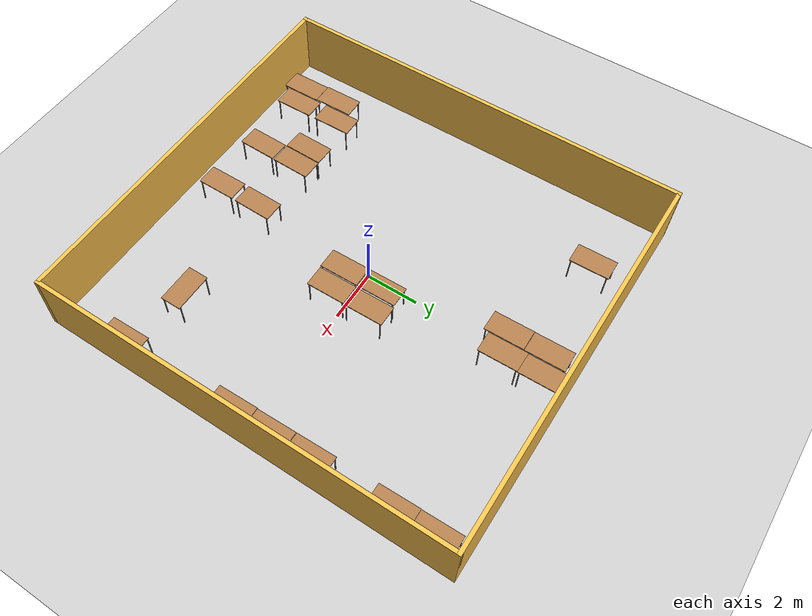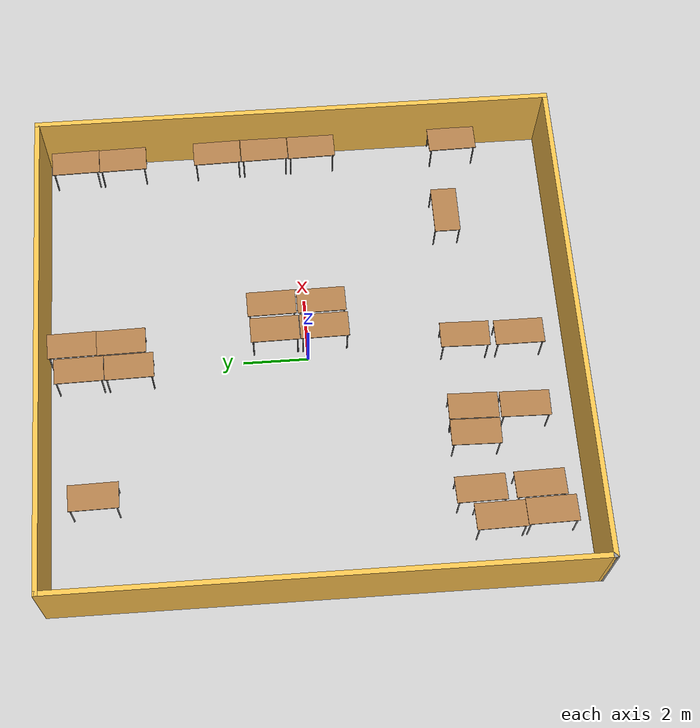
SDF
<sdf version="1.7">
 <world name="default">
  <light name="sun" type="directional">
   <pose>0 0 10 0 -0 0</pose>
   <diffuse>0.8 0.8 0.8 1</diffuse>
   <specular>0.2 0.2 0.2 1</specular>
   <attenuation>
    <range>1000</range>
    <constant>0.9</constant>
    <linear>0.01</linear>
    <quadratic>0.001</quadratic>
   </attenuation>
   <direction>-0.5 0.1 -0.9</direction>
   <spot><inner_angle>0</inner_angle><outer_angle>0</outer_angle><falloff>0</falloff></spot>
  </light>
  <model name="ground_plane">
   <static>1</static>
   <link name="link">
    <collision name="collision">
     <geometry><plane><normal>0 0 1</normal><size>100 100</size></plane></geometry>
     <surface>
      <contact><collide_bitmask>65535</collide_bitmask></contact>
      <friction><ode><mu>100</mu><mu2>50</mu2></ode></friction>
     </surface>
    </collision>
    <visual name="visual">
     <cast_shadows>0</cast_shadows>
     <geometry><plane><normal>0 0 1</normal><size>100 100</size></plane></geometry>
     <material>
      <script><uri>file://media/materials/scripts/gazebo.material</uri><name>Gazebo/Grey</name></script>
     </material>
    </visual>
   </link>
  </model>
  <gravity>0 0 -9.8</gravity>
  <magnetic_field>6e-06 2.3e-05 -4.2e-05</magnetic_field>
  <atmosphere type="adiabatic"/>
  <physics type="ode">
   <max_step_size>0.001</max_step_size>
   <real_time_factor>1</real_time_factor>
   <real_time_update_rate>1000</real_time_update_rate>
  </physics>
  <scene><ambient>0.4 0.4 0.4 1</ambient><background>0.7 0.7 0.7 1</background><shadows>1</shadows></scene>
  <spherical_coordinates>
   <surface_model>EARTH_WGS84</surface_model>
   <latitude_deg>0</latitude_deg>
   <longitude_deg>0</longitude_deg>
   <elevation>0</elevation>
   <heading_deg>0</heading_deg>
  </spherical_coordinates>
  <model name="RRC">
   <link name="Wall_0">
    <collision name="Wall_0_Collision">
     <geometry><box><size>16.15 0.15 2.5</size></box></geometry>
     <pose>0 0 1.25 0 -0 0</pose>
    </collision>
    <visual name="Wall_0_Visual">
     <pose>0 0 1.25 0 -0 0</pose>
     <geometry><box><size>16.15 0.15 2.5</size></box></geometry>
     <material>
      <script><uri>file://media/materials/scripts/gazebo.material</uri><name>Gazebo/Grey</name></script>
      <ambient>1 0.764706 0.305882 1</ambient>
     </material>
     <meta><layer>0</layer></meta>
    </visual>
    <pose>-7.5 0 0 0 -0 1.5708</pose>
   </link>
   <link name="Wall_1">
    <collision name="Wall_1_Collision">
     <geometry><box><size>15.15 0.15 2.5</size></box></geometry>
     <pose>0 0 1.25 0 -0 0</pose>
    </collision>
    <visual name="Wall_1_Visual">
     <pose>0 0 1.25 0 -0 0</pose>
     <geometry><box><size>15.15 0.15 2.5</size></box></geometry>
     <material>
      <script><uri>file://media/materials/scripts/gazebo.material</uri><name>Gazebo/Grey</name></script>
      <ambient>1 0.764706 0.305882 1</ambient>
     </material>
     <meta><layer>0</layer></meta>
    </visual>
    <pose>0 8 0 0 -0 0</pose>
   </link>
   <link name="Wall_2">
    <collision name="Wall_2_Collision">
     <geometry><box><size>16.15 0.15 2.5</size></box></geometry>
     <pose>0 0 1.25 0 -0 0</pose>
    </collision>
    <visual name="Wall_2_Visual">
     <pose>0 0 1.25 0 -0 0</pose>
     <geometry><box><size>16.15 0.15 2.5</size></box></geometry>
     <material>
      <script><uri>file://media/materials/scripts/gazebo.material</uri><name>Gazebo/Grey</name></script>
      <ambient>1 0.764706 0.305882 1</ambient>
     </material>
     <meta><layer>0</layer></meta>
    </visual>
    <pose>7.5 0 0 0 -0 -1.5708</pose>
   </link>
   <link name="Wall_3">
    <collision name="Wall_3_Collision">
     <geometry><box><size>15.15 0.15 2.5</size></box></geometry>
     <pose>0 0 1.25 0 -0 0</pose>
    </collision>
    <visual name="Wall_3_Visual">
     <pose>0 0 1.25 0 -0 0</pose>
     <geometry><box><size>15.15 0.15 2.5</size></box></geometry>
     <material>
      <script><uri>file://media/materials/scripts/gazebo.material</uri><name>Gazebo/Grey</name></script>
      <ambient>1 0.764706 0.305882 1</ambient>
     </material>
     <meta><layer>0</layer></meta>
    </visual>
    <pose>0 -8 0 0 -0 3.14159</pose>
   </link>
   <link name="Wall_4">
    <collision name="Wall_4_Collision">
     <geometry><box><size>0.15 0.15 2.5</size></box></geometry>
     <pose>0 0 1.25 0 -0 0</pose>
    </collision>
    <visual name="Wall_4_Visual">
     <pose>0 0 1.25 0 -0 0</pose>
     <geometry><box><size>0.15 0.15 2.5</size></box></geometry>
     <material>
      <script><uri>file://media/materials/scripts/gazebo.material</uri><name>Gazebo/Grey</name></script>
      <ambient>1 1 1 1</ambient>
     </material>
     <meta><layer>0</layer></meta>
    </visual>
    <pose>-7.5 -8 0 0 -0 0</pose>
   </link>
   <static>1</static>
  </model>
  <model name="table_clone_0_clone_0">
   <static>1</static>
   <link name="link1">
    <collision name="surface">
     <pose>0 0 1 0 -0 0</pose>
     <geometry><box><size>1.5 0.8 0.03</size></box></geometry>
     <surface><friction><ode><mu>0.6</mu><mu2>0.6</mu2></ode></friction></surface>
    </collision>
    <visual name="visual1">
     <pose>0 0 1 0 -0 0</pose>
     <geometry><box><size>1.5 0.8 0.03</size></box></geometry>
     <material>
      <script><uri>file://media/materials/scripts/gazebo.material</uri><name>Gazebo/Wood</name></script>
     </material>
    </visual>
    <collision name="front_left_leg">
     <pose>0.68 0.38 0.5 0 -0 0</pose>
     <geometry><cylinder><radius>0.02</radius><length>1</length></cylinder></geometry>
    </collision>
    <visual name="front_left_leg">
     <pose>0.68 0.38 0.5 0 -0 0</pose>
     <geometry><cylinder><radius>0.02</radius><length>1</length></cylinder></geometry>
     <material>
      <script><uri>file://media/materials/scripts/gazebo.material</uri><name>Gazebo/Grey</name></script>
     </material>
    </visual>
    <collision name="front_right_leg">
     <pose>0.68 -0.38 0.5 0 -0 0</pose>
     <geometry><cylinder><radius>0.02</radius><length>1</length></cylinder></geometry>
    </collision>
    <visual name="front_right_leg">
     <pose>0.68 -0.38 0.5 0 -0 0</pose>
     <geometry><cylinder><radius>0.02</radius><length>1</length></cylinder></geometry>
     <material>
      <script><uri>file://media/materials/scripts/gazebo.material</uri><name>Gazebo/Grey</name></script>
     </material>
    </visual>
    <collision name="back_right_leg">
     <pose>-0.68 -0.38 0.5 0 -0 0</pose>
     <geometry><cylinder><radius>0.02</radius><length>1</length></cylinder></geometry>
    </collision>
    <visual name="back_right_leg">
     <pose>-0.68 -0.38 0.5 0 -0 0</pose>
     <geometry><cylinder><radius>0.02</radius><length>1</length></cylinder></geometry>
     <material>
      <script><uri>file://media/materials/scripts/gazebo.material</uri><name>Gazebo/Grey</name></script>
     </material>
    </visual>
    <collision name="back_left_leg">
     <pose>-0.68 0.38 0.5 0 -0 0</pose>
     <geometry><cylinder><radius>0.02</radius><length>1</length></cylinder></geometry>
    </collision>
    <visual name="back_left_leg">
     <pose>-0.68 0.38 0.5 0 -0 0</pose>
     <geometry><cylinder><radius>0.02</radius><length>1</length></cylinder></geometry>
     <material>
      <script><uri>file://media/materials/scripts/gazebo.material</uri><name>Gazebo/Grey</name></script>
     </material>
    </visual>
   </link>
   <pose>-4.33016 6.56363 0 0 -0 1.58908</pose>
  </model>
  <model name="table_clone_0_clone_clone">
   <static>1</static>
   <link name="link2">
    <collision name="surface">
     <pose>0 0 1 0 -0 0</pose>
     <geometry><box><size>1.5 0.8 0.03</size></box></geometry>
     <surface><friction><ode><mu>0.6</mu><mu2>0.6</mu2></ode></friction></surface>
    </collision>
    <visual name="visual1">
     <pose>0 0 1 0 -0 0</pose>
     <geometry><box><size>1.5 0.8 0.03</size></box></geometry>
     <material>
      <script><uri>file://media/materials/scripts/gazebo.material</uri><name>Gazebo/Wood</name></script>
     </material>
    </visual>
    <collision name="front_left_leg">
     <pose>0.68 0.38 0.5 0 -0 0</pose>
     <geometry><cylinder><radius>0.02</radius><length>1</length></cylinder></geometry>
    </collision>
    <visual name="front_left_leg">
     <pose>0.68 0.38 0.5 0 -0 0</pose>
     <geometry><cylinder><radius>0.02</radius><length>1</length></cylinder></geometry>
     <material>
      <script><uri>file://media/materials/scripts/gazebo.material</uri><name>Gazebo/Grey</name></script>
     </material>
    </visual>
    <collision name="front_right_leg">
     <pose>0.68 -0.38 0.5 0 -0 0</pose>
     <geometry><cylinder><radius>0.02</radius><length>1</length></cylinder></geometry>
    </collision>
    <visual name="front_right_leg">
     <pose>0.68 -0.38 0.5 0 -0 0</pose>
     <geometry><cylinder><radius>0.02</radius><length>1</length></cylinder></geometry>
     <material>
      <script><uri>file://media/materials/scripts/gazebo.material</uri><name>Gazebo/Grey</name></script>
     </material>
    </visual>
    <collision name="back_right_leg">
     <pose>-0.68 -0.38 0.5 0 -0 0</pose>
     <geometry><cylinder><radius>0.02</radius><length>1</length></cylinder></geometry>
    </collision>
    <visual name="back_right_leg">
     <pose>-0.68 -0.38 0.5 0 -0 0</pose>
     <geometry><cylinder><radius>0.02</radius><length>1</length></cylinder></geometry>
     <material>
      <script><uri>file://media/materials/scripts/gazebo.material</uri><name>Gazebo/Grey</name></script>
     </material>
    </visual>
    <collision name="back_left_leg">
     <pose>-0.68 0.38 0.5 0 -0 0</pose>
     <geometry><cylinder><radius>0.02</radius><length>1</length></cylinder></geometry>
    </collision>
    <visual name="back_left_leg">
     <pose>-0.68 0.38 0.5 0 -0 0</pose>
     <geometry><cylinder><radius>0.02</radius><length>1</length></cylinder></geometry>
     <material>
      <script><uri>file://media/materials/scripts/gazebo.material</uri><name>Gazebo/Grey</name></script>
     </material>
    </visual>
   </link>
   <pose>-0.295656 6.95966 0 0 -0 1.58908</pose>
  </model>
  <model name="table_clone_0_clone_clone_0">
   <static>1</static>
   <link name="link3">
    <collision name="surface">
     <pose>0 0 1 0 -0 0</pose>
     <geometry><box><size>1.5 0.8 0.03</size></box></geometry>
     <surface><friction><ode><mu>0.6</mu><mu2>0.6</mu2></ode></friction></surface>
    </collision>
    <visual name="visual1">
     <pose>0 0 1 0 -0 0</pose>
     <geometry><box><size>1.5 0.8 0.03</size></box></geometry>
     <material>
      <script><uri>file://media/materials/scripts/gazebo.material</uri><name>Gazebo/Wood</name></script>
     </material>
    </visual>
    <collision name="front_left_leg">
     <pose>0.68 0.38 0.5 0 -0 0</pose>
     <geometry><cylinder><radius>0.02</radius><length>1</length></cylinder></geometry>
    </collision>
    <visual name="front_left_leg">
     <pose>0.68 0.38 0.5 0 -0 0</pose>
     <geometry><cylinder><radius>0.02</radius><length>1</length></cylinder></geometry>
     <material>
      <script><uri>file://media/materials/scripts/gazebo.material</uri><name>Gazebo/Grey</name></script>
     </material>
    </visual>
    <collision name="front_right_leg">
     <pose>0.68 -0.38 0.5 0 -0 0</pose>
     <geometry><cylinder><radius>0.02</radius><length>1</length></cylinder></geometry>
    </collision>
    <visual name="front_right_leg">
     <pose>0.68 -0.38 0.5 0 -0 0</pose>
     <geometry><cylinder><radius>0.02</radius><length>1</length></cylinder></geometry>
     <material>
      <script><uri>file://media/materials/scripts/gazebo.material</uri><name>Gazebo/Grey</name></script>
     </material>
    </visual>
    <collision name="back_right_leg">
     <pose>-0.68 -0.38 0.5 0 -0 0</pose>
     <geometry><cylinder><radius>0.02</radius><length>1</length></cylinder></geometry>
    </collision>
    <visual name="back_right_leg">
     <pose>-0.68 -0.38 0.5 0 -0 0</pose>
     <geometry><cylinder><radius>0.02</radius><length>1</length></cylinder></geometry>
     <material>
      <script><uri>file://media/materials/scripts/gazebo.material</uri><name>Gazebo/Grey</name></script>
     </material>
    </visual>
    <collision name="back_left_leg">
     <pose>-0.68 0.38 0.5 0 -0 0</pose>
     <geometry><cylinder><radius>0.02</radius><length>1</length></cylinder></geometry>
    </collision>
    <visual name="back_left_leg">
     <pose>-0.68 0.38 0.5 0 -0 0</pose>
     <geometry><cylinder><radius>0.02</radius><length>1</length></cylinder></geometry>
     <material>
      <script><uri>file://media/materials/scripts/gazebo.material</uri><name>Gazebo/Grey</name></script>
     </material>
    </visual>
   </link>
   <pose>-0.274415 5.44749 0 0 -0 1.58908</pose>
  </model>
  <model name="table_clone_0_clone_clone_clone">
   <static>1</static>
   <link name="link4">
    <collision name="surface">
     <pose>0 0 1 0 -0 0</pose>
     <geometry><box><size>1.5 0.8 0.03</size></box></geometry>
     <surface><friction><ode><mu>0.6</mu><mu2>0.6</mu2></ode></friction></surface>
    </collision>
    <visual name="visual1">
     <pose>0 0 1 0 -0 0</pose>
     <geometry><box><size>1.5 0.8 0.03</size></box></geometry>
     <material>
      <script><uri>file://media/materials/scripts/gazebo.material</uri><name>Gazebo/Wood</name></script>
     </material>
    </visual>
    <collision name="front_left_leg">
     <pose>0.68 0.38 0.5 0 -0 0</pose>
     <geometry><cylinder><radius>0.02</radius><length>1</length></cylinder></geometry>
    </collision>
    <visual name="front_left_leg">
     <pose>0.68 0.38 0.5 0 -0 0</pose>
     <geometry><cylinder><radius>0.02</radius><length>1</length></cylinder></geometry>
     <material>
      <script><uri>file://media/materials/scripts/gazebo.material</uri><name>Gazebo/Grey</name></script>
     </material>
    </visual>
    <collision name="front_right_leg">
     <pose>0.68 -0.38 0.5 0 -0 0</pose>
     <geometry><cylinder><radius>0.02</radius><length>1</length></cylinder></geometry>
    </collision>
    <visual name="front_right_leg">
     <pose>0.68 -0.38 0.5 0 -0 0</pose>
     <geometry><cylinder><radius>0.02</radius><length>1</length></cylinder></geometry>
     <material>
      <script><uri>file://media/materials/scripts/gazebo.material</uri><name>Gazebo/Grey</name></script>
     </material>
    </visual>
    <collision name="back_right_leg">
     <pose>-0.68 -0.38 0.5 0 -0 0</pose>
     <geometry><cylinder><radius>0.02</radius><length>1</length></cylinder></geometry>
    </collision>
    <visual name="back_right_leg">
     <pose>-0.68 -0.38 0.5 0 -0 0</pose>
     <geometry><cylinder><radius>0.02</radius><length>1</length></cylinder></geometry>
     <material>
      <script><uri>file://media/materials/scripts/gazebo.material</uri><name>Gazebo/Grey</name></script>
     </material>
    </visual>
    <collision name="back_left_leg">
     <pose>-0.68 0.38 0.5 0 -0 0</pose>
     <geometry><cylinder><radius>0.02</radius><length>1</length></cylinder></geometry>
    </collision>
    <visual name="back_left_leg">
     <pose>-0.68 0.38 0.5 0 -0 0</pose>
     <geometry><cylinder><radius>0.02</radius><length>1</length></cylinder></geometry>
     <material>
      <script><uri>file://media/materials/scripts/gazebo.material</uri><name>Gazebo/Grey</name></script>
     </material>
    </visual>
   </link>
   <pose>0.539492 7.15927 0 0 -0 1.58908</pose>
  </model>
  <model name="table_clone_0_clone_clone_clone_0">
   <static>1</static>
   <link name="link5">
    <collision name="surface">
     <pose>0 0 1 0 -0 0</pose>
     <geometry><box><size>1.5 0.8 0.03</size></box></geometry>
     <surface><friction><ode><mu>0.6</mu><mu2>0.6</mu2></ode></friction></surface>
    </collision>
    <visual name="visual1">
     <pose>0 0 1 0 -0 0</pose>
     <geometry><box><size>1.5 0.8 0.03</size></box></geometry>
     <material>
      <script><uri>file://media/materials/scripts/gazebo.material</uri><name>Gazebo/Wood</name></script>
     </material>
    </visual>
    <collision name="front_left_leg">
     <pose>0.68 0.38 0.5 0 -0 0</pose>
     <geometry><cylinder><radius>0.02</radius><length>1</length></cylinder></geometry>
    </collision>
    <visual name="front_left_leg">
     <pose>0.68 0.38 0.5 0 -0 0</pose>
     <geometry><cylinder><radius>0.02</radius><length>1</length></cylinder></geometry>
     <material>
      <script><uri>file://media/materials/scripts/gazebo.material</uri><name>Gazebo/Grey</name></script>
     </material>
    </visual>
    <collision name="front_right_leg">
     <pose>0.68 -0.38 0.5 0 -0 0</pose>
     <geometry><cylinder><radius>0.02</radius><length>1</length></cylinder></geometry>
    </collision>
    <visual name="front_right_leg">
     <pose>0.68 -0.38 0.5 0 -0 0</pose>
     <geometry><cylinder><radius>0.02</radius><length>1</length></cylinder></geometry>
     <material>
      <script><uri>file://media/materials/scripts/gazebo.material</uri><name>Gazebo/Grey</name></script>
     </material>
    </visual>
    <collision name="back_right_leg">
     <pose>-0.68 -0.38 0.5 0 -0 0</pose>
     <geometry><cylinder><radius>0.02</radius><length>1</length></cylinder></geometry>
    </collision>
    <visual name="back_right_leg">
     <pose>-0.68 -0.38 0.5 0 -0 0</pose>
     <geometry><cylinder><radius>0.02</radius><length>1</length></cylinder></geometry>
     <material>
      <script><uri>file://media/materials/scripts/gazebo.material</uri><name>Gazebo/Grey</name></script>
     </material>
    </visual>
    <collision name="back_left_leg">
     <pose>-0.68 0.38 0.5 0 -0 0</pose>
     <geometry><cylinder><radius>0.02</radius><length>1</length></cylinder></geometry>
    </collision>
    <visual name="back_left_leg">
     <pose>-0.68 0.38 0.5 0 -0 0</pose>
     <geometry><cylinder><radius>0.02</radius><length>1</length></cylinder></geometry>
     <material>
      <script><uri>file://media/materials/scripts/gazebo.material</uri><name>Gazebo/Grey</name></script>
     </material>
    </visual>
   </link>
   <pose>0.553868 5.6672 0 0 -0 1.58908</pose>
  </model>
  <model name="table_clone_0_clone_1">
   <static>1</static>
   <link name="link6">
    <collision name="surface">
     <pose>0 0 1 0 -0 0</pose>
     <geometry><box><size>1.5 0.8 0.03</size></box></geometry>
     <surface><friction><ode><mu>0.6</mu><mu2>0.6</mu2></ode></friction></surface>
    </collision>
    <visual name="visual1">
     <pose>0 0 1 0 -0 0</pose>
     <geometry><box><size>1.5 0.8 0.03</size></box></geometry>
     <material>
      <script><uri>file://media/materials/scripts/gazebo.material</uri><name>Gazebo/Wood</name></script>
     </material>
    </visual>
    <collision name="front_left_leg">
     <pose>0.68 0.38 0.5 0 -0 0</pose>
     <geometry><cylinder><radius>0.02</radius><length>1</length></cylinder></geometry>
    </collision>
    <visual name="front_left_leg">
     <pose>0.68 0.38 0.5 0 -0 0</pose>
     <geometry><cylinder><radius>0.02</radius><length>1</length></cylinder></geometry>
     <material>
      <script><uri>file://media/materials/scripts/gazebo.material</uri><name>Gazebo/Grey</name></script>
     </material>
    </visual>
    <collision name="front_right_leg">
     <pose>0.68 -0.38 0.5 0 -0 0</pose>
     <geometry><cylinder><radius>0.02</radius><length>1</length></cylinder></geometry>
    </collision>
    <visual name="front_right_leg">
     <pose>0.68 -0.38 0.5 0 -0 0</pose>
     <geometry><cylinder><radius>0.02</radius><length>1</length></cylinder></geometry>
     <material>
      <script><uri>file://media/materials/scripts/gazebo.material</uri><name>Gazebo/Grey</name></script>
     </material>
    </visual>
    <collision name="back_right_leg">
     <pose>-0.68 -0.38 0.5 0 -0 0</pose>
     <geometry><cylinder><radius>0.02</radius><length>1</length></cylinder></geometry>
    </collision>
    <visual name="back_right_leg">
     <pose>-0.68 -0.38 0.5 0 -0 0</pose>
     <geometry><cylinder><radius>0.02</radius><length>1</length></cylinder></geometry>
     <material>
      <script><uri>file://media/materials/scripts/gazebo.material</uri><name>Gazebo/Grey</name></script>
     </material>
    </visual>
    <collision name="back_left_leg">
     <pose>-0.68 0.38 0.5 0 -0 0</pose>
     <geometry><cylinder><radius>0.02</radius><length>1</length></cylinder></geometry>
    </collision>
    <visual name="back_left_leg">
     <pose>-0.68 0.38 0.5 0 -0 0</pose>
     <geometry><cylinder><radius>0.02</radius><length>1</length></cylinder></geometry>
     <material>
      <script><uri>file://media/materials/scripts/gazebo.material</uri><name>Gazebo/Grey</name></script>
     </material>
    </visual>
   </link>
   <pose>6.94327 6.99918 0 0 -0 1.58908</pose>
  </model>
  <model name="table_clone_0_clone_2">
   <static>1</static>
   <link name="link7">
    <collision name="surface">
     <pose>0 0 1 0 -0 0</pose>
     <geometry><box><size>1.5 0.8 0.03</size></box></geometry>
     <surface><friction><ode><mu>0.6</mu><mu2>0.6</mu2></ode></friction></surface>
    </collision>
    <visual name="visual1">
     <pose>0 0 1 0 -0 0</pose>
     <geometry><box><size>1.5 0.8 0.03</size></box></geometry>
     <material>
      <script><uri>file://media/materials/scripts/gazebo.material</uri><name>Gazebo/Wood</name></script>
     </material>
    </visual>
    <collision name="front_left_leg">
     <pose>0.68 0.38 0.5 0 -0 0</pose>
     <geometry><cylinder><radius>0.02</radius><length>1</length></cylinder></geometry>
    </collision>
    <visual name="front_left_leg">
     <pose>0.68 0.38 0.5 0 -0 0</pose>
     <geometry><cylinder><radius>0.02</radius><length>1</length></cylinder></geometry>
     <material>
      <script><uri>file://media/materials/scripts/gazebo.material</uri><name>Gazebo/Grey</name></script>
     </material>
    </visual>
    <collision name="front_right_leg">
     <pose>0.68 -0.38 0.5 0 -0 0</pose>
     <geometry><cylinder><radius>0.02</radius><length>1</length></cylinder></geometry>
    </collision>
    <visual name="front_right_leg">
     <pose>0.68 -0.38 0.5 0 -0 0</pose>
     <geometry><cylinder><radius>0.02</radius><length>1</length></cylinder></geometry>
     <material>
      <script><uri>file://media/materials/scripts/gazebo.material</uri><name>Gazebo/Grey</name></script>
     </material>
    </visual>
    <collision name="back_right_leg">
     <pose>-0.68 -0.38 0.5 0 -0 0</pose>
     <geometry><cylinder><radius>0.02</radius><length>1</length></cylinder></geometry>
    </collision>
    <visual name="back_right_leg">
     <pose>-0.68 -0.38 0.5 0 -0 0</pose>
     <geometry><cylinder><radius>0.02</radius><length>1</length></cylinder></geometry>
     <material>
      <script><uri>file://media/materials/scripts/gazebo.material</uri><name>Gazebo/Grey</name></script>
     </material>
    </visual>
    <collision name="back_left_leg">
     <pose>-0.68 0.38 0.5 0 -0 0</pose>
     <geometry><cylinder><radius>0.02</radius><length>1</length></cylinder></geometry>
    </collision>
    <visual name="back_left_leg">
     <pose>-0.68 0.38 0.5 0 -0 0</pose>
     <geometry><cylinder><radius>0.02</radius><length>1</length></cylinder></geometry>
     <material>
      <script><uri>file://media/materials/scripts/gazebo.material</uri><name>Gazebo/Grey</name></script>
     </material>
    </visual>
   </link>
   <pose>6.95814 5.4935 0 0 -0 1.58908</pose>
  </model>
  <model name="table_clone_0_clone_4">
   <static>1</static>
   <link name="link8">
    <collision name="surface">
     <pose>0 0 1 0 -0 0</pose>
     <geometry><box><size>1.5 0.8 0.03</size></box></geometry>
     <surface><friction><ode><mu>0.6</mu><mu2>0.6</mu2></ode></friction></surface>
    </collision>
    <visual name="visual1">
     <pose>0 0 1 0 -0 0</pose>
     <geometry><box><size>1.5 0.8 0.03</size></box></geometry>
     <material>
      <script><uri>file://media/materials/scripts/gazebo.material</uri><name>Gazebo/Wood</name></script>
     </material>
    </visual>
    <collision name="front_left_leg">
     <pose>0.68 0.38 0.5 0 -0 0</pose>
     <geometry><cylinder><radius>0.02</radius><length>1</length></cylinder></geometry>
    </collision>
    <visual name="front_left_leg">
     <pose>0.68 0.38 0.5 0 -0 0</pose>
     <geometry><cylinder><radius>0.02</radius><length>1</length></cylinder></geometry>
     <material>
      <script><uri>file://media/materials/scripts/gazebo.material</uri><name>Gazebo/Grey</name></script>
     </material>
    </visual>
    <collision name="front_right_leg">
     <pose>0.68 -0.38 0.5 0 -0 0</pose>
     <geometry><cylinder><radius>0.02</radius><length>1</length></cylinder></geometry>
    </collision>
    <visual name="front_right_leg">
     <pose>0.68 -0.38 0.5 0 -0 0</pose>
     <geometry><cylinder><radius>0.02</radius><length>1</length></cylinder></geometry>
     <material>
      <script><uri>file://media/materials/scripts/gazebo.material</uri><name>Gazebo/Grey</name></script>
     </material>
    </visual>
    <collision name="back_right_leg">
     <pose>-0.68 -0.38 0.5 0 -0 0</pose>
     <geometry><cylinder><radius>0.02</radius><length>1</length></cylinder></geometry>
    </collision>
    <visual name="back_right_leg">
     <pose>-0.68 -0.38 0.5 0 -0 0</pose>
     <geometry><cylinder><radius>0.02</radius><length>1</length></cylinder></geometry>
     <material>
      <script><uri>file://media/materials/scripts/gazebo.material</uri><name>Gazebo/Grey</name></script>
     </material>
    </visual>
    <collision name="back_left_leg">
     <pose>-0.68 0.38 0.5 0 -0 0</pose>
     <geometry><cylinder><radius>0.02</radius><length>1</length></cylinder></geometry>
    </collision>
    <visual name="back_left_leg">
     <pose>-0.68 0.38 0.5 0 -0 0</pose>
     <geometry><cylinder><radius>0.02</radius><length>1</length></cylinder></geometry>
     <material>
      <script><uri>file://media/materials/scripts/gazebo.material</uri><name>Gazebo/Grey</name></script>
     </material>
    </visual>
   </link>
   <pose>7.01065 2.4699 0 0 -0 1.58908</pose>
  </model>
  <model name="table_clone_0_clone_5">
   <static>1</static>
   <link name="link9">
    <collision name="surface">
     <pose>0 0 1 0 -0 0</pose>
     <geometry><box><size>1.5 0.8 0.03</size></box></geometry>
     <surface><friction><ode><mu>0.6</mu><mu2>0.6</mu2></ode></friction></surface>
    </collision>
    <visual name="visual1">
     <pose>0 0 1 0 -0 0</pose>
     <geometry><box><size>1.5 0.8 0.03</size></box></geometry>
     <material>
      <script><uri>file://media/materials/scripts/gazebo.material</uri><name>Gazebo/Wood</name></script>
     </material>
    </visual>
    <collision name="front_left_leg">
     <pose>0.68 0.38 0.5 0 -0 0</pose>
     <geometry><cylinder><radius>0.02</radius><length>1</length></cylinder></geometry>
    </collision>
    <visual name="front_left_leg">
     <pose>0.68 0.38 0.5 0 -0 0</pose>
     <geometry><cylinder><radius>0.02</radius><length>1</length></cylinder></geometry>
     <material>
      <script><uri>file://media/materials/scripts/gazebo.material</uri><name>Gazebo/Grey</name></script>
     </material>
    </visual>
    <collision name="front_right_leg">
     <pose>0.68 -0.38 0.5 0 -0 0</pose>
     <geometry><cylinder><radius>0.02</radius><length>1</length></cylinder></geometry>
    </collision>
    <visual name="front_right_leg">
     <pose>0.68 -0.38 0.5 0 -0 0</pose>
     <geometry><cylinder><radius>0.02</radius><length>1</length></cylinder></geometry>
     <material>
      <script><uri>file://media/materials/scripts/gazebo.material</uri><name>Gazebo/Grey</name></script>
     </material>
    </visual>
    <collision name="back_right_leg">
     <pose>-0.68 -0.38 0.5 0 -0 0</pose>
     <geometry><cylinder><radius>0.02</radius><length>1</length></cylinder></geometry>
    </collision>
    <visual name="back_right_leg">
     <pose>-0.68 -0.38 0.5 0 -0 0</pose>
     <geometry><cylinder><radius>0.02</radius><length>1</length></cylinder></geometry>
     <material>
      <script><uri>file://media/materials/scripts/gazebo.material</uri><name>Gazebo/Grey</name></script>
     </material>
    </visual>
    <collision name="back_left_leg">
     <pose>-0.68 0.38 0.5 0 -0 0</pose>
     <geometry><cylinder><radius>0.02</radius><length>1</length></cylinder></geometry>
    </collision>
    <visual name="back_left_leg">
     <pose>-0.68 0.38 0.5 0 -0 0</pose>
     <geometry><cylinder><radius>0.02</radius><length>1</length></cylinder></geometry>
     <material>
      <script><uri>file://media/materials/scripts/gazebo.material</uri><name>Gazebo/Grey</name></script>
     </material>
    </visual>
   </link>
   <pose>7.03829 0.952201 0 0 -0 1.58908</pose>
  </model>
  <model name="table_clone_0_clone_6">
   <static>1</static>
   <link name="link10">
    <collision name="surface">
     <pose>0 0 1 0 -0 0</pose>
     <geometry><box><size>1.5 0.8 0.03</size></box></geometry>
     <surface><friction><ode><mu>0.6</mu><mu2>0.6</mu2></ode></friction></surface>
    </collision>
    <visual name="visual1">
     <pose>0 0 1 0 -0 0</pose>
     <geometry><box><size>1.5 0.8 0.03</size></box></geometry>
     <material>
      <script><uri>file://media/materials/scripts/gazebo.material</uri><name>Gazebo/Wood</name></script>
     </material>
    </visual>
    <collision name="front_left_leg">
     <pose>0.68 0.38 0.5 0 -0 0</pose>
     <geometry><cylinder><radius>0.02</radius><length>1</length></cylinder></geometry>
    </collision>
    <visual name="front_left_leg">
     <pose>0.68 0.38 0.5 0 -0 0</pose>
     <geometry><cylinder><radius>0.02</radius><length>1</length></cylinder></geometry>
     <material>
      <script><uri>file://media/materials/scripts/gazebo.material</uri><name>Gazebo/Grey</name></script>
     </material>
    </visual>
    <collision name="front_right_leg">
     <pose>0.68 -0.38 0.5 0 -0 0</pose>
     <geometry><cylinder><radius>0.02</radius><length>1</length></cylinder></geometry>
    </collision>
    <visual name="front_right_leg">
     <pose>0.68 -0.38 0.5 0 -0 0</pose>
     <geometry><cylinder><radius>0.02</radius><length>1</length></cylinder></geometry>
     <material>
      <script><uri>file://media/materials/scripts/gazebo.material</uri><name>Gazebo/Grey</name></script>
     </material>
    </visual>
    <collision name="back_right_leg">
     <pose>-0.68 -0.38 0.5 0 -0 0</pose>
     <geometry><cylinder><radius>0.02</radius><length>1</length></cylinder></geometry>
    </collision>
    <visual name="back_right_leg">
     <pose>-0.68 -0.38 0.5 0 -0 0</pose>
     <geometry><cylinder><radius>0.02</radius><length>1</length></cylinder></geometry>
     <material>
      <script><uri>file://media/materials/scripts/gazebo.material</uri><name>Gazebo/Grey</name></script>
     </material>
    </visual>
    <collision name="back_left_leg">
     <pose>-0.68 0.38 0.5 0 -0 0</pose>
     <geometry><cylinder><radius>0.02</radius><length>1</length></cylinder></geometry>
    </collision>
    <visual name="back_left_leg">
     <pose>-0.68 0.38 0.5 0 -0 0</pose>
     <geometry><cylinder><radius>0.02</radius><length>1</length></cylinder></geometry>
     <material>
      <script><uri>file://media/materials/scripts/gazebo.material</uri><name>Gazebo/Grey</name></script>
     </material>
    </visual>
   </link>
   <pose>7.04645 -0.560802 0 0 -0 1.58908</pose>
  </model>
  <model name="table_clone_0_clone_9">
   <static>1</static>
   <link name="link11">
    <collision name="surface">
     <pose>0 0 1 0 -0 0</pose>
     <geometry><box><size>1.5 0.8 0.03</size></box></geometry>
     <surface><friction><ode><mu>0.6</mu><mu2>0.6</mu2></ode></friction></surface>
    </collision>
    <visual name="visual1">
     <pose>0 0 1 0 -0 0</pose>
     <geometry><box><size>1.5 0.8 0.03</size></box></geometry>
     <material>
      <script><uri>file://media/materials/scripts/gazebo.material</uri><name>Gazebo/Wood</name></script>
     </material>
    </visual>
    <collision name="front_left_leg">
     <pose>0.68 0.38 0.5 0 -0 0</pose>
     <geometry><cylinder><radius>0.02</radius><length>1</length></cylinder></geometry>
    </collision>
    <visual name="front_left_leg">
     <pose>0.68 0.38 0.5 0 -0 0</pose>
     <geometry><cylinder><radius>0.02</radius><length>1</length></cylinder></geometry>
     <material>
      <script><uri>file://media/materials/scripts/gazebo.material</uri><name>Gazebo/Grey</name></script>
     </material>
    </visual>
    <collision name="front_right_leg">
     <pose>0.68 -0.38 0.5 0 -0 0</pose>
     <geometry><cylinder><radius>0.02</radius><length>1</length></cylinder></geometry>
    </collision>
    <visual name="front_right_leg">
     <pose>0.68 -0.38 0.5 0 -0 0</pose>
     <geometry><cylinder><radius>0.02</radius><length>1</length></cylinder></geometry>
     <material>
      <script><uri>file://media/materials/scripts/gazebo.material</uri><name>Gazebo/Grey</name></script>
     </material>
    </visual>
    <collision name="back_right_leg">
     <pose>-0.68 -0.38 0.5 0 -0 0</pose>
     <geometry><cylinder><radius>0.02</radius><length>1</length></cylinder></geometry>
    </collision>
    <visual name="back_right_leg">
     <pose>-0.68 -0.38 0.5 0 -0 0</pose>
     <geometry><cylinder><radius>0.02</radius><length>1</length></cylinder></geometry>
     <material>
      <script><uri>file://media/materials/scripts/gazebo.material</uri><name>Gazebo/Grey</name></script>
     </material>
    </visual>
    <collision name="back_left_leg">
     <pose>-0.68 0.38 0.5 0 -0 0</pose>
     <geometry><cylinder><radius>0.02</radius><length>1</length></cylinder></geometry>
    </collision>
    <visual name="back_left_leg">
     <pose>-0.68 0.38 0.5 0 -0 0</pose>
     <geometry><cylinder><radius>0.02</radius><length>1</length></cylinder></geometry>
     <material>
      <script><uri>file://media/materials/scripts/gazebo.material</uri><name>Gazebo/Grey</name></script>
     </material>
    </visual>
   </link>
   <pose>7.02703 -5.11024 0 0 -0 1.58908</pose>
  </model>
  <model name="table_clone_0_clone_clone_1">
   <static>1</static>
   <link name="link47">
    <collision name="surface">
     <pose>0 0 1 0 -0 0</pose>
     <geometry><box><size>1.5 0.8 0.03</size></box></geometry>
     <surface><friction><ode><mu>0.6</mu><mu2>0.6</mu2></ode></friction></surface>
    </collision>
    <visual name="visual1">
     <pose>0 0 1 0 -0 0</pose>
     <geometry><box><size>1.5 0.8 0.03</size></box></geometry>
     <material>
      <script><uri>file://media/materials/scripts/gazebo.material</uri><name>Gazebo/Wood</name></script>
     </material>
    </visual>
    <collision name="front_left_leg">
     <pose>0.68 0.38 0.5 0 -0 0</pose>
     <geometry><cylinder><radius>0.02</radius><length>1</length></cylinder></geometry>
    </collision>
    <visual name="front_left_leg">
     <pose>0.68 0.38 0.5 0 -0 0</pose>
     <geometry><cylinder><radius>0.02</radius><length>1</length></cylinder></geometry>
     <material>
      <script><uri>file://media/materials/scripts/gazebo.material</uri><name>Gazebo/Grey</name></script>
     </material>
    </visual>
    <collision name="front_right_leg">
     <pose>0.68 -0.38 0.5 0 -0 0</pose>
     <geometry><cylinder><radius>0.02</radius><length>1</length></cylinder></geometry>
    </collision>
    <visual name="front_right_leg">
     <pose>0.68 -0.38 0.5 0 -0 0</pose>
     <geometry><cylinder><radius>0.02</radius><length>1</length></cylinder></geometry>
     <material>
      <script><uri>file://media/materials/scripts/gazebo.material</uri><name>Gazebo/Grey</name></script>
     </material>
    </visual>
    <collision name="back_right_leg">
     <pose>-0.68 -0.38 0.5 0 -0 0</pose>
     <geometry><cylinder><radius>0.02</radius><length>1</length></cylinder></geometry>
    </collision>
    <visual name="back_right_leg">
     <pose>-0.68 -0.38 0.5 0 -0 0</pose>
     <geometry><cylinder><radius>0.02</radius><length>1</length></cylinder></geometry>
     <material>
      <script><uri>file://media/materials/scripts/gazebo.material</uri><name>Gazebo/Grey</name></script>
     </material>
    </visual>
    <collision name="back_left_leg">
     <pose>-0.68 0.38 0.5 0 -0 0</pose>
     <geometry><cylinder><radius>0.02</radius><length>1</length></cylinder></geometry>
    </collision>
    <visual name="back_left_leg">
     <pose>-0.68 0.38 0.5 0 -0 0</pose>
     <geometry><cylinder><radius>0.02</radius><length>1</length></cylinder></geometry>
     <material>
      <script><uri>file://media/materials/scripts/gazebo.material</uri><name>Gazebo/Grey</name></script>
     </material>
    </visual>
   </link>
   <pose>-5.62606 -6.7098 0 0 -0 1.58908</pose>
  </model>
  <model name="table_clone_0_clone_clone_2">
   <static>1</static>
   <link name="link48">
    <collision name="surface">
     <pose>0 0 1 0 -0 0</pose>
     <geometry><box><size>1.5 0.8 0.03</size></box></geometry>
     <surface><friction><ode><mu>0.6</mu><mu2>0.6</mu2></ode></friction></surface>
    </collision>
    <visual name="visual1">
     <pose>0 0 1 0 -0 0</pose>
     <geometry><box><size>1.5 0.8 0.03</size></box></geometry>
     <material>
      <script><uri>file://media/materials/scripts/gazebo.material</uri><name>Gazebo/Wood</name></script>
     </material>
    </visual>
    <collision name="front_left_leg">
     <pose>0.68 0.38 0.5 0 -0 0</pose>
     <geometry><cylinder><radius>0.02</radius><length>1</length></cylinder></geometry>
    </collision>
    <visual name="front_left_leg">
     <pose>0.68 0.38 0.5 0 -0 0</pose>
     <geometry><cylinder><radius>0.02</radius><length>1</length></cylinder></geometry>
     <material>
      <script><uri>file://media/materials/scripts/gazebo.material</uri><name>Gazebo/Grey</name></script>
     </material>
    </visual>
    <collision name="front_right_leg">
     <pose>0.68 -0.38 0.5 0 -0 0</pose>
     <geometry><cylinder><radius>0.02</radius><length>1</length></cylinder></geometry>
    </collision>
    <visual name="front_right_leg">
     <pose>0.68 -0.38 0.5 0 -0 0</pose>
     <geometry><cylinder><radius>0.02</radius><length>1</length></cylinder></geometry>
     <material>
      <script><uri>file://media/materials/scripts/gazebo.material</uri><name>Gazebo/Grey</name></script>
     </material>
    </visual>
    <collision name="back_right_leg">
     <pose>-0.68 -0.38 0.5 0 -0 0</pose>
     <geometry><cylinder><radius>0.02</radius><length>1</length></cylinder></geometry>
    </collision>
    <visual name="back_right_leg">
     <pose>-0.68 -0.38 0.5 0 -0 0</pose>
     <geometry><cylinder><radius>0.02</radius><length>1</length></cylinder></geometry>
     <material>
      <script><uri>file://media/materials/scripts/gazebo.material</uri><name>Gazebo/Grey</name></script>
     </material>
    </visual>
    <collision name="back_left_leg">
     <pose>-0.68 0.38 0.5 0 -0 0</pose>
     <geometry><cylinder><radius>0.02</radius><length>1</length></cylinder></geometry>
    </collision>
    <visual name="back_left_leg">
     <pose>-0.68 0.38 0.5 0 -0 0</pose>
     <geometry><cylinder><radius>0.02</radius><length>1</length></cylinder></geometry>
     <material>
      <script><uri>file://media/materials/scripts/gazebo.material</uri><name>Gazebo/Grey</name></script>
     </material>
    </visual>
   </link>
   <pose>-5.68516 -5.20679 0 0 -0 1.58908</pose>
  </model>
  <model name="table_clone_0_clone_clone_2_clone">
   <static>1</static>
   <link name="link49">
    <collision name="surface">
     <pose>0 0 1 0 -0 0</pose>
     <geometry><box><size>1.5 0.8 0.03</size></box></geometry>
     <surface><friction><ode><mu>0.6</mu><mu2>0.6</mu2></ode></friction></surface>
    </collision>
    <visual name="visual1">
     <pose>0 0 1 0 -0 0</pose>
     <geometry><box><size>1.5 0.8 0.03</size></box></geometry>
     <material>
      <script><uri>file://media/materials/scripts/gazebo.material</uri><name>Gazebo/Wood</name></script>
     </material>
    </visual>
    <collision name="front_left_leg">
     <pose>0.68 0.38 0.5 0 -0 0</pose>
     <geometry><cylinder><radius>0.02</radius><length>1</length></cylinder></geometry>
    </collision>
    <visual name="front_left_leg">
     <pose>0.68 0.38 0.5 0 -0 0</pose>
     <geometry><cylinder><radius>0.02</radius><length>1</length></cylinder></geometry>
     <material>
      <script><uri>file://media/materials/scripts/gazebo.material</uri><name>Gazebo/Grey</name></script>
     </material>
    </visual>
    <collision name="front_right_leg">
     <pose>0.68 -0.38 0.5 0 -0 0</pose>
     <geometry><cylinder><radius>0.02</radius><length>1</length></cylinder></geometry>
    </collision>
    <visual name="front_right_leg">
     <pose>0.68 -0.38 0.5 0 -0 0</pose>
     <geometry><cylinder><radius>0.02</radius><length>1</length></cylinder></geometry>
     <material>
      <script><uri>file://media/materials/scripts/gazebo.material</uri><name>Gazebo/Grey</name></script>
     </material>
    </visual>
    <collision name="back_right_leg">
     <pose>-0.68 -0.38 0.5 0 -0 0</pose>
     <geometry><cylinder><radius>0.02</radius><length>1</length></cylinder></geometry>
    </collision>
    <visual name="back_right_leg">
     <pose>-0.68 -0.38 0.5 0 -0 0</pose>
     <geometry><cylinder><radius>0.02</radius><length>1</length></cylinder></geometry>
     <material>
      <script><uri>file://media/materials/scripts/gazebo.material</uri><name>Gazebo/Grey</name></script>
     </material>
    </visual>
    <collision name="back_left_leg">
     <pose>-0.68 0.38 0.5 0 -0 0</pose>
     <geometry><cylinder><radius>0.02</radius><length>1</length></cylinder></geometry>
    </collision>
    <visual name="back_left_leg">
     <pose>-0.68 0.38 0.5 0 -0 0</pose>
     <geometry><cylinder><radius>0.02</radius><length>1</length></cylinder></geometry>
     <material>
      <script><uri>file://media/materials/scripts/gazebo.material</uri><name>Gazebo/Grey</name></script>
     </material>
    </visual>
   </link>
   <pose>-4.83975 -4.71811 0 0 -0 1.58908</pose>
  </model>
  <model name="table_clone_0_clone_clone_2_clone_0">
   <static>1</static>
   <link name="link50">
    <collision name="surface">
     <pose>0 0 1 0 -0 0</pose>
     <geometry><box><size>1.5 0.8 0.03</size></box></geometry>
     <surface><friction><ode><mu>0.6</mu><mu2>0.6</mu2></ode></friction></surface>
    </collision>
    <visual name="visual1">
     <pose>0 0 1 0 -0 0</pose>
     <geometry><box><size>1.5 0.8 0.03</size></box></geometry>
     <material>
      <script><uri>file://media/materials/scripts/gazebo.material</uri><name>Gazebo/Wood</name></script>
     </material>
    </visual>
    <collision name="front_left_leg">
     <pose>0.68 0.38 0.5 0 -0 0</pose>
     <geometry><cylinder><radius>0.02</radius><length>1</length></cylinder></geometry>
    </collision>
    <visual name="front_left_leg">
     <pose>0.68 0.38 0.5 0 -0 0</pose>
     <geometry><cylinder><radius>0.02</radius><length>1</length></cylinder></geometry>
     <material>
      <script><uri>file://media/materials/scripts/gazebo.material</uri><name>Gazebo/Grey</name></script>
     </material>
    </visual>
    <collision name="front_right_leg">
     <pose>0.68 -0.38 0.5 0 -0 0</pose>
     <geometry><cylinder><radius>0.02</radius><length>1</length></cylinder></geometry>
    </collision>
    <visual name="front_right_leg">
     <pose>0.68 -0.38 0.5 0 -0 0</pose>
     <geometry><cylinder><radius>0.02</radius><length>1</length></cylinder></geometry>
     <material>
      <script><uri>file://media/materials/scripts/gazebo.material</uri><name>Gazebo/Grey</name></script>
     </material>
    </visual>
    <collision name="back_right_leg">
     <pose>-0.68 -0.38 0.5 0 -0 0</pose>
     <geometry><cylinder><radius>0.02</radius><length>1</length></cylinder></geometry>
    </collision>
    <visual name="back_right_leg">
     <pose>-0.68 -0.38 0.5 0 -0 0</pose>
     <geometry><cylinder><radius>0.02</radius><length>1</length></cylinder></geometry>
     <material>
      <script><uri>file://media/materials/scripts/gazebo.material</uri><name>Gazebo/Grey</name></script>
     </material>
    </visual>
    <collision name="back_left_leg">
     <pose>-0.68 0.38 0.5 0 -0 0</pose>
     <geometry><cylinder><radius>0.02</radius><length>1</length></cylinder></geometry>
    </collision>
    <visual name="back_left_leg">
     <pose>-0.68 0.38 0.5 0 -0 0</pose>
     <geometry><cylinder><radius>0.02</radius><length>1</length></cylinder></geometry>
     <material>
      <script><uri>file://media/materials/scripts/gazebo.material</uri><name>Gazebo/Grey</name></script>
     </material>
    </visual>
   </link>
   <pose>-4.79726 -6.46943 0 0 -0 1.58908</pose>
  </model>
  <model name="table_clone_clone_clone">
   <static>1</static>
   <link name="link51">
    <collision name="surface">
     <pose>0 0 1 0 -0 0</pose>
     <geometry><box><size>1.5 0.8 0.03</size></box></geometry>
     <surface><friction><ode><mu>0.6</mu><mu2>0.6</mu2></ode></friction></surface>
    </collision>
    <visual name="visual1">
     <pose>0 0 1 0 -0 0</pose>
     <geometry><box><size>1.5 0.8 0.03</size></box></geometry>
     <material>
      <script><uri>file://media/materials/scripts/gazebo.material</uri><name>Gazebo/Wood</name></script>
     </material>
    </visual>
    <collision name="front_left_leg">
     <pose>0.68 0.38 0.5 0 -0 0</pose>
     <geometry><cylinder><radius>0.02</radius><length>1</length></cylinder></geometry>
    </collision>
    <visual name="front_left_leg">
     <pose>0.68 0.38 0.5 0 -0 0</pose>
     <geometry><cylinder><radius>0.02</radius><length>1</length></cylinder></geometry>
     <material>
      <script><uri>file://media/materials/scripts/gazebo.material</uri><name>Gazebo/Grey</name></script>
     </material>
    </visual>
    <collision name="front_right_leg">
     <pose>0.68 -0.38 0.5 0 -0 0</pose>
     <geometry><cylinder><radius>0.02</radius><length>1</length></cylinder></geometry>
    </collision>
    <visual name="front_right_leg">
     <pose>0.68 -0.38 0.5 0 -0 0</pose>
     <geometry><cylinder><radius>0.02</radius><length>1</length></cylinder></geometry>
     <material>
      <script><uri>file://media/materials/scripts/gazebo.material</uri><name>Gazebo/Grey</name></script>
     </material>
    </visual>
    <collision name="back_right_leg">
     <pose>-0.68 -0.38 0.5 0 -0 0</pose>
     <geometry><cylinder><radius>0.02</radius><length>1</length></cylinder></geometry>
    </collision>
    <visual name="back_right_leg">
     <pose>-0.68 -0.38 0.5 0 -0 0</pose>
     <geometry><cylinder><radius>0.02</radius><length>1</length></cylinder></geometry>
     <material>
      <script><uri>file://media/materials/scripts/gazebo.material</uri><name>Gazebo/Grey</name></script>
     </material>
    </visual>
    <collision name="back_left_leg">
     <pose>-0.68 0.38 0.5 0 -0 0</pose>
     <geometry><cylinder><radius>0.02</radius><length>1</length></cylinder></geometry>
    </collision>
    <visual name="back_left_leg">
     <pose>-0.68 0.38 0.5 0 -0 0</pose>
     <geometry><cylinder><radius>0.02</radius><length>1</length></cylinder></geometry>
     <material>
      <script><uri>file://media/materials/scripts/gazebo.material</uri><name>Gazebo/Grey</name></script>
     </material>
    </visual>
   </link>
   <pose>-3.07867 -4.76943 0 0 0 -1.59028</pose>
  </model>
  <model name="table_clone_clone_clone_0">
   <static>1</static>
   <link name="link52">
    <collision name="surface">
     <pose>0 0 1 0 -0 0</pose>
     <geometry><box><size>1.5 0.8 0.03</size></box></geometry>
     <surface><friction><ode><mu>0.6</mu><mu2>0.6</mu2></ode></friction></surface>
    </collision>
    <visual name="visual1">
     <pose>0 0 1 0 -0 0</pose>
     <geometry><box><size>1.5 0.8 0.03</size></box></geometry>
     <material>
      <script><uri>file://media/materials/scripts/gazebo.material</uri><name>Gazebo/Wood</name></script>
     </material>
    </visual>
    <collision name="front_left_leg">
     <pose>0.68 0.38 0.5 0 -0 0</pose>
     <geometry><cylinder><radius>0.02</radius><length>1</length></cylinder></geometry>
    </collision>
    <visual name="front_left_leg">
     <pose>0.68 0.38 0.5 0 -0 0</pose>
     <geometry><cylinder><radius>0.02</radius><length>1</length></cylinder></geometry>
     <material>
      <script><uri>file://media/materials/scripts/gazebo.material</uri><name>Gazebo/Grey</name></script>
     </material>
    </visual>
    <collision name="front_right_leg">
     <pose>0.68 -0.38 0.5 0 -0 0</pose>
     <geometry><cylinder><radius>0.02</radius><length>1</length></cylinder></geometry>
    </collision>
    <visual name="front_right_leg">
     <pose>0.68 -0.38 0.5 0 -0 0</pose>
     <geometry><cylinder><radius>0.02</radius><length>1</length></cylinder></geometry>
     <material>
      <script><uri>file://media/materials/scripts/gazebo.material</uri><name>Gazebo/Grey</name></script>
     </material>
    </visual>
    <collision name="back_right_leg">
     <pose>-0.68 -0.38 0.5 0 -0 0</pose>
     <geometry><cylinder><radius>0.02</radius><length>1</length></cylinder></geometry>
    </collision>
    <visual name="back_right_leg">
     <pose>-0.68 -0.38 0.5 0 -0 0</pose>
     <geometry><cylinder><radius>0.02</radius><length>1</length></cylinder></geometry>
     <material>
      <script><uri>file://media/materials/scripts/gazebo.material</uri><name>Gazebo/Grey</name></script>
     </material>
    </visual>
    <collision name="back_left_leg">
     <pose>-0.68 0.38 0.5 0 -0 0</pose>
     <geometry><cylinder><radius>0.02</radius><length>1</length></cylinder></geometry>
    </collision>
    <visual name="back_left_leg">
     <pose>-0.68 0.38 0.5 0 -0 0</pose>
     <geometry><cylinder><radius>0.02</radius><length>1</length></cylinder></geometry>
     <material>
      <script><uri>file://media/materials/scripts/gazebo.material</uri><name>Gazebo/Grey</name></script>
     </material>
    </visual>
   </link>
   <pose>-2.25255 -4.77765 0 0 0 -1.59028</pose>
  </model>
  <model name="table_clone_clone_clone_0_clone">
   <static>1</static>
   <link name="link53">
    <collision name="surface">
     <pose>0 0 1 0 -0 0</pose>
     <geometry><box><size>1.5 0.8 0.03</size></box></geometry>
     <surface><friction><ode><mu>0.6</mu><mu2>0.6</mu2></ode></friction></surface>
    </collision>
    <visual name="visual1">
     <pose>0 0 1 0 -0 0</pose>
     <geometry><box><size>1.5 0.8 0.03</size></box></geometry>
     <material>
      <script><uri>file://media/materials/scripts/gazebo.material</uri><name>Gazebo/Wood</name></script>
     </material>
    </visual>
    <collision name="front_left_leg">
     <pose>0.68 0.38 0.5 0 -0 0</pose>
     <geometry><cylinder><radius>0.02</radius><length>1</length></cylinder></geometry>
    </collision>
    <visual name="front_left_leg">
     <pose>0.68 0.38 0.5 0 -0 0</pose>
     <geometry><cylinder><radius>0.02</radius><length>1</length></cylinder></geometry>
     <material>
      <script><uri>file://media/materials/scripts/gazebo.material</uri><name>Gazebo/Grey</name></script>
     </material>
    </visual>
    <collision name="front_right_leg">
     <pose>0.68 -0.38 0.5 0 -0 0</pose>
     <geometry><cylinder><radius>0.02</radius><length>1</length></cylinder></geometry>
    </collision>
    <visual name="front_right_leg">
     <pose>0.68 -0.38 0.5 0 -0 0</pose>
     <geometry><cylinder><radius>0.02</radius><length>1</length></cylinder></geometry>
     <material>
      <script><uri>file://media/materials/scripts/gazebo.material</uri><name>Gazebo/Grey</name></script>
     </material>
    </visual>
    <collision name="back_right_leg">
     <pose>-0.68 -0.38 0.5 0 -0 0</pose>
     <geometry><cylinder><radius>0.02</radius><length>1</length></cylinder></geometry>
    </collision>
    <visual name="back_right_leg">
     <pose>-0.68 -0.38 0.5 0 -0 0</pose>
     <geometry><cylinder><radius>0.02</radius><length>1</length></cylinder></geometry>
     <material>
      <script><uri>file://media/materials/scripts/gazebo.material</uri><name>Gazebo/Grey</name></script>
     </material>
    </visual>
    <collision name="back_left_leg">
     <pose>-0.68 0.38 0.5 0 -0 0</pose>
     <geometry><cylinder><radius>0.02</radius><length>1</length></cylinder></geometry>
    </collision>
    <visual name="back_left_leg">
     <pose>-0.68 0.38 0.5 0 -0 0</pose>
     <geometry><cylinder><radius>0.02</radius><length>1</length></cylinder></geometry>
     <material>
      <script><uri>file://media/materials/scripts/gazebo.material</uri><name>Gazebo/Grey</name></script>
     </material>
    </visual>
   </link>
   <pose>0.097904 -4.78362 0 0 0 -1.59028</pose>
  </model>
  <model name="table_clone_clone_0">
   <static>1</static>
   <link name="link54">
    <collision name="surface">
     <pose>0 0 1 0 -0 0</pose>
     <geometry><box><size>1.5 0.8 0.03</size></box></geometry>
     <surface><friction><ode><mu>0.6</mu><mu2>0.6</mu2></ode></friction></surface>
    </collision>
    <visual name="visual1">
     <pose>0 0 1 0 -0 0</pose>
     <geometry><box><size>1.5 0.8 0.03</size></box></geometry>
     <material>
      <script><uri>file://media/materials/scripts/gazebo.material</uri><name>Gazebo/Wood</name></script>
     </material>
    </visual>
    <collision name="front_left_leg">
     <pose>0.68 0.38 0.5 0 -0 0</pose>
     <geometry><cylinder><radius>0.02</radius><length>1</length></cylinder></geometry>
    </collision>
    <visual name="front_left_leg">
     <pose>0.68 0.38 0.5 0 -0 0</pose>
     <geometry><cylinder><radius>0.02</radius><length>1</length></cylinder></geometry>
     <material>
      <script><uri>file://media/materials/scripts/gazebo.material</uri><name>Gazebo/Grey</name></script>
     </material>
    </visual>
    <collision name="front_right_leg">
     <pose>0.68 -0.38 0.5 0 -0 0</pose>
     <geometry><cylinder><radius>0.02</radius><length>1</length></cylinder></geometry>
    </collision>
    <visual name="front_right_leg">
     <pose>0.68 -0.38 0.5 0 -0 0</pose>
     <geometry><cylinder><radius>0.02</radius><length>1</length></cylinder></geometry>
     <material>
      <script><uri>file://media/materials/scripts/gazebo.material</uri><name>Gazebo/Grey</name></script>
     </material>
    </visual>
    <collision name="back_right_leg">
     <pose>-0.68 -0.38 0.5 0 -0 0</pose>
     <geometry><cylinder><radius>0.02</radius><length>1</length></cylinder></geometry>
    </collision>
    <visual name="back_right_leg">
     <pose>-0.68 -0.38 0.5 0 -0 0</pose>
     <geometry><cylinder><radius>0.02</radius><length>1</length></cylinder></geometry>
     <material>
      <script><uri>file://media/materials/scripts/gazebo.material</uri><name>Gazebo/Grey</name></script>
     </material>
    </visual>
    <collision name="back_left_leg">
     <pose>-0.68 0.38 0.5 0 -0 0</pose>
     <geometry><cylinder><radius>0.02</radius><length>1</length></cylinder></geometry>
    </collision>
    <visual name="back_left_leg">
     <pose>-0.68 0.38 0.5 0 -0 0</pose>
     <geometry><cylinder><radius>0.02</radius><length>1</length></cylinder></geometry>
     <material>
      <script><uri>file://media/materials/scripts/gazebo.material</uri><name>Gazebo/Grey</name></script>
     </material>
    </visual>
   </link>
   <pose>0.074544 -6.44489 0 0 0 -1.57013</pose>
  </model>
  <model name="table_clone_1">
   <static>1</static>
   <link name="link55">
    <collision name="surface">
     <pose>0 0 1 0 -0 0</pose>
     <geometry><box><size>1.5 0.8 0.03</size></box></geometry>
     <surface><friction><ode><mu>0.6</mu><mu2>0.6</mu2></ode></friction></surface>
    </collision>
    <visual name="visual1">
     <pose>0 0 1 0 -0 0</pose>
     <geometry><box><size>1.5 0.8 0.03</size></box></geometry>
     <material>
      <script><uri>file://media/materials/scripts/gazebo.material</uri><name>Gazebo/Wood</name></script>
     </material>
    </visual>
    <collision name="front_left_leg">
     <pose>0.68 0.38 0.5 0 -0 0</pose>
     <geometry><cylinder><radius>0.02</radius><length>1</length></cylinder></geometry>
    </collision>
    <visual name="front_left_leg">
     <pose>0.68 0.38 0.5 0 -0 0</pose>
     <geometry><cylinder><radius>0.02</radius><length>1</length></cylinder></geometry>
     <material>
      <script><uri>file://media/materials/scripts/gazebo.material</uri><name>Gazebo/Grey</name></script>
     </material>
    </visual>
    <collision name="front_right_leg">
     <pose>0.68 -0.38 0.5 0 -0 0</pose>
     <geometry><cylinder><radius>0.02</radius><length>1</length></cylinder></geometry>
    </collision>
    <visual name="front_right_leg">
     <pose>0.68 -0.38 0.5 0 -0 0</pose>
     <geometry><cylinder><radius>0.02</radius><length>1</length></cylinder></geometry>
     <material>
      <script><uri>file://media/materials/scripts/gazebo.material</uri><name>Gazebo/Grey</name></script>
     </material>
    </visual>
    <collision name="back_right_leg">
     <pose>-0.68 -0.38 0.5 0 -0 0</pose>
     <geometry><cylinder><radius>0.02</radius><length>1</length></cylinder></geometry>
    </collision>
    <visual name="back_right_leg">
     <pose>-0.68 -0.38 0.5 0 -0 0</pose>
     <geometry><cylinder><radius>0.02</radius><length>1</length></cylinder></geometry>
     <material>
      <script><uri>file://media/materials/scripts/gazebo.material</uri><name>Gazebo/Grey</name></script>
     </material>
    </visual>
    <collision name="back_left_leg">
     <pose>-0.68 0.38 0.5 0 -0 0</pose>
     <geometry><cylinder><radius>0.02</radius><length>1</length></cylinder></geometry>
    </collision>
    <visual name="back_left_leg">
     <pose>-0.68 0.38 0.5 0 -0 0</pose>
     <geometry><cylinder><radius>0.02</radius><length>1</length></cylinder></geometry>
     <material>
      <script><uri>file://media/materials/scripts/gazebo.material</uri><name>Gazebo/Grey</name></script>
     </material>
    </visual>
   </link>
   <pose>4.42862 -4.64955 0 0 -0 0</pose>
  </model>
  <model name="table_clone_2_clone_clone_clone">
   <static>1</static>
   <link name="link59">
    <collision name="surface">
     <pose>0 0 1 0 -0 0</pose>
     <geometry><box><size>1.5 0.8 0.03</size></box></geometry>
     <surface><friction><ode><mu>0.6</mu><mu2>0.6</mu2></ode></friction></surface>
    </collision>
    <visual name="visual1">
     <pose>0 0 1 0 -0 0</pose>
     <geometry><box><size>1.5 0.8 0.03</size></box></geometry>
     <material>
      <script><uri>file://media/materials/scripts/gazebo.material</uri><name>Gazebo/Wood</name></script>
     </material>
    </visual>
    <collision name="front_left_leg">
     <pose>0.68 0.38 0.5 0 -0 0</pose>
     <geometry><cylinder><radius>0.02</radius><length>1</length></cylinder></geometry>
    </collision>
    <visual name="front_left_leg">
     <pose>0.68 0.38 0.5 0 -0 0</pose>
     <geometry><cylinder><radius>0.02</radius><length>1</length></cylinder></geometry>
     <material>
      <script><uri>file://media/materials/scripts/gazebo.material</uri><name>Gazebo/Grey</name></script>
     </material>
    </visual>
    <collision name="front_right_leg">
     <pose>0.68 -0.38 0.5 0 -0 0</pose>
     <geometry><cylinder><radius>0.02</radius><length>1</length></cylinder></geometry>
    </collision>
    <visual name="front_right_leg">
     <pose>0.68 -0.38 0.5 0 -0 0</pose>
     <geometry><cylinder><radius>0.02</radius><length>1</length></cylinder></geometry>
     <material>
      <script><uri>file://media/materials/scripts/gazebo.material</uri><name>Gazebo/Grey</name></script>
     </material>
    </visual>
    <collision name="back_right_leg">
     <pose>-0.68 -0.38 0.5 0 -0 0</pose>
     <geometry><cylinder><radius>0.02</radius><length>1</length></cylinder></geometry>
    </collision>
    <visual name="back_right_leg">
     <pose>-0.68 -0.38 0.5 0 -0 0</pose>
     <geometry><cylinder><radius>0.02</radius><length>1</length></cylinder></geometry>
     <material>
      <script><uri>file://media/materials/scripts/gazebo.material</uri><name>Gazebo/Grey</name></script>
     </material>
    </visual>
    <collision name="back_left_leg">
     <pose>-0.68 0.38 0.5 0 -0 0</pose>
     <geometry><cylinder><radius>0.02</radius><length>1</length></cylinder></geometry>
    </collision>
    <visual name="back_left_leg">
     <pose>-0.68 0.38 0.5 0 -0 0</pose>
     <geometry><cylinder><radius>0.02</radius><length>1</length></cylinder></geometry>
     <material>
      <script><uri>file://media/materials/scripts/gazebo.material</uri><name>Gazebo/Grey</name></script>
     </material>
    </visual>
   </link>
   <pose>0.664986 0.980658 0 0 0 -1.55798</pose>
  </model>
  <model name="table_clone_2_clone_clone_clone_0">
   <static>1</static>
   <link name="link60">
    <collision name="surface">
     <pose>0 0 1 0 -0 0</pose>
     <geometry><box><size>1.5 0.8 0.03</size></box></geometry>
     <surface><friction><ode><mu>0.6</mu><mu2>0.6</mu2></ode></friction></surface>
    </collision>
    <visual name="visual1">
     <pose>0 0 1 0 -0 0</pose>
     <geometry><box><size>1.5 0.8 0.03</size></box></geometry>
     <material>
      <script><uri>file://media/materials/scripts/gazebo.material</uri><name>Gazebo/Wood</name></script>
     </material>
    </visual>
    <collision name="front_left_leg">
     <pose>0.68 0.38 0.5 0 -0 0</pose>
     <geometry><cylinder><radius>0.02</radius><length>1</length></cylinder></geometry>
    </collision>
    <visual name="front_left_leg">
     <pose>0.68 0.38 0.5 0 -0 0</pose>
     <geometry><cylinder><radius>0.02</radius><length>1</length></cylinder></geometry>
     <material>
      <script><uri>file://media/materials/scripts/gazebo.material</uri><name>Gazebo/Grey</name></script>
     </material>
    </visual>
    <collision name="front_right_leg">
     <pose>0.68 -0.38 0.5 0 -0 0</pose>
     <geometry><cylinder><radius>0.02</radius><length>1</length></cylinder></geometry>
    </collision>
    <visual name="front_right_leg">
     <pose>0.68 -0.38 0.5 0 -0 0</pose>
     <geometry><cylinder><radius>0.02</radius><length>1</length></cylinder></geometry>
     <material>
      <script><uri>file://media/materials/scripts/gazebo.material</uri><name>Gazebo/Grey</name></script>
     </material>
    </visual>
    <collision name="back_right_leg">
     <pose>-0.68 -0.38 0.5 0 -0 0</pose>
     <geometry><cylinder><radius>0.02</radius><length>1</length></cylinder></geometry>
    </collision>
    <visual name="back_right_leg">
     <pose>-0.68 -0.38 0.5 0 -0 0</pose>
     <geometry><cylinder><radius>0.02</radius><length>1</length></cylinder></geometry>
     <material>
      <script><uri>file://media/materials/scripts/gazebo.material</uri><name>Gazebo/Grey</name></script>
     </material>
    </visual>
    <collision name="back_left_leg">
     <pose>-0.68 0.38 0.5 0 -0 0</pose>
     <geometry><cylinder><radius>0.02</radius><length>1</length></cylinder></geometry>
    </collision>
    <visual name="back_left_leg">
     <pose>-0.68 0.38 0.5 0 -0 0</pose>
     <geometry><cylinder><radius>0.02</radius><length>1</length></cylinder></geometry>
     <material>
      <script><uri>file://media/materials/scripts/gazebo.material</uri><name>Gazebo/Grey</name></script>
     </material>
    </visual>
   </link>
   <pose>0.684996 -0.53817 0 0 0 -1.55798</pose>
  </model>
  <model name="table_clone_clone_clone_0_clone_0">
   <static>1</static>
   <link name="link62">
    <collision name="surface">
     <pose>0 0 1 0 -0 0</pose>
     <geometry><box><size>1.5 0.8 0.03</size></box></geometry>
     <surface><friction><ode><mu>0.6</mu><mu2>0.6</mu2></ode></friction></surface>
    </collision>
    <visual name="visual1">
     <pose>0 0 1 0 -0 0</pose>
     <geometry><box><size>1.5 0.8 0.03</size></box></geometry>
     <material>
      <script><uri>file://media/materials/scripts/gazebo.material</uri><name>Gazebo/Wood</name></script>
     </material>
    </visual>
    <collision name="front_left_leg">
     <pose>0.68 0.38 0.5 0 -0 0</pose>
     <geometry><cylinder><radius>0.02</radius><length>1</length></cylinder></geometry>
    </collision>
    <visual name="front_left_leg">
     <pose>0.68 0.38 0.5 0 -0 0</pose>
     <geometry><cylinder><radius>0.02</radius><length>1</length></cylinder></geometry>
     <material>
      <script><uri>file://media/materials/scripts/gazebo.material</uri><name>Gazebo/Grey</name></script>
     </material>
    </visual>
    <collision name="front_right_leg">
     <pose>0.68 -0.38 0.5 0 -0 0</pose>
     <geometry><cylinder><radius>0.02</radius><length>1</length></cylinder></geometry>
    </collision>
    <visual name="front_right_leg">
     <pose>0.68 -0.38 0.5 0 -0 0</pose>
     <geometry><cylinder><radius>0.02</radius><length>1</length></cylinder></geometry>
     <material>
      <script><uri>file://media/materials/scripts/gazebo.material</uri><name>Gazebo/Grey</name></script>
     </material>
    </visual>
    <collision name="back_right_leg">
     <pose>-0.68 -0.38 0.5 0 -0 0</pose>
     <geometry><cylinder><radius>0.02</radius><length>1</length></cylinder></geometry>
    </collision>
    <visual name="back_right_leg">
     <pose>-0.68 -0.38 0.5 0 -0 0</pose>
     <geometry><cylinder><radius>0.02</radius><length>1</length></cylinder></geometry>
     <material>
      <script><uri>file://media/materials/scripts/gazebo.material</uri><name>Gazebo/Grey</name></script>
     </material>
    </visual>
    <collision name="back_left_leg">
     <pose>-0.68 0.38 0.5 0 -0 0</pose>
     <geometry><cylinder><radius>0.02</radius><length>1</length></cylinder></geometry>
    </collision>
    <visual name="back_left_leg">
     <pose>-0.68 0.38 0.5 0 -0 0</pose>
     <geometry><cylinder><radius>0.02</radius><length>1</length></cylinder></geometry>
     <material>
      <script><uri>file://media/materials/scripts/gazebo.material</uri><name>Gazebo/Grey</name></script>
     </material>
    </visual>
   </link>
   <pose>-2.28813 -6.33451 0 0 0 -1.59028</pose>
  </model>
  <model name="cardboard_box_0">
   <pose>3.96847 0.977565 -1.0418e+07 0 -0 0</pose>
   <link name="link63">
    <pose>3.96847 0.977565 0.149 0 -0 0</pose>
    <inertial>
     <inertia><ixx>1</ixx><ixy>0</ixy><ixz>0</ixz><iyy>1</iyy><iyz>0</iyz><izz>1</izz></inertia>
     <mass>1</mass>
    </inertial>
    <velocity>0 0 0 0 -0 0</velocity>
    <acceleration>0 -1.9e-05 0 0.000128 2e-06 0</acceleration>
    <wrench>1e-06 -3.8e-05 1e-06 0 -0 0</wrench>
   </link>
   <scale>1 1 1</scale>
  </model>
  <model name="cardboard_box_1">
   <pose>0.006438 -3.96264 -1.0418e+07 0 -0 0</pose>
   <link name="link64">
    <pose>0.006438 -3.96264 0.149 0 -0 0</pose>
    <inertial>
     <inertia><ixx>1</ixx><ixy>0</ixy><ixz>0</ixz><iyy>1</iyy><iyz>0</iyz><izz>1</izz></inertia>
     <mass>1</mass>
    </inertial>
    <velocity>0 0 0 0 -0 0</velocity>
    <acceleration>0 1.9e-05 0 -0.000128 -2e-06 0</acceleration>
    <wrench>-1e-06 3.8e-05 -1e-06 0 -0 0</wrench>
   </link>
   <scale>1 1 1</scale>
  </model>
  <model name="cardboard_box_2">
   <pose>-4.88373 2.96722 -1.0418e+07 0 -0 0</pose>
   <link name="link65">
    <pose>-4.88373 2.96722 0.149 0 -0 0</pose>
    <inertial>
     <inertia><ixx>1</ixx><ixy>0</ixy><ixz>0</ixz><iyy>1</iyy><iyz>0</iyz><izz>1</izz></inertia>
     <mass>1</mass>
    </inertial>
    <velocity>0 0 0 0 -0 0</velocity>
    <acceleration>0 -1.9e-05 0 0.000128 2e-06 0</acceleration>
    <wrench>1e-06 -3.8e-05 1e-06 0 -0 0</wrench>
   </link>
   <scale>1 1 1</scale>
  </model>
  <model name="cardboard_box_3">
   <pose>-0.0158 3.98725 -1.0418e+07 2e-06 -2e-06 -0</pose>
   <link name="link66">
    <pose>-0.0158 3.98725 0.14951 2e-06 -2e-06 -0</pose>
    <inertial>
     <inertia><ixx>1</ixx><ixy>0</ixy><ixz>0</ixz><iyy>1</iyy><iyz>0</iyz><izz>1</izz></inertia>
     <mass>1</mass>
    </inertial>
    <velocity>0 0 0 0 -0 0</velocity>
    <acceleration>0 1.1e-05 0 -7.2e-05 1e-06 0</acceleration>
    <wrench>0 2.2e-05 0 0 -0 0</wrench>
   </link>
   <scale>1 1 1</scale>
  </model>
  <model name="table_clone_2_clone_clone_clone_clone">
   <static>1</static>
   <link name="link67">
    <collision name="surface">
     <pose>0 0 1 0 -0 0</pose>
     <geometry><box><size>1.5 0.8 0.03</size></box></geometry>
     <surface><friction><ode><mu>0.6</mu><mu2>0.6</mu2></ode></friction></surface>
    </collision>
    <visual name="visual1">
     <pose>0 0 1 0 -0 0</pose>
     <geometry><box><size>1.5 0.8 0.03</size></box></geometry>
     <material>
      <script><uri>file://media/materials/scripts/gazebo.material</uri><name>Gazebo/Wood</name></script>
     </material>
    </visual>
    <collision name="front_left_leg">
     <pose>0.68 0.38 0.5 0 -0 0</pose>
     <geometry><cylinder><radius>0.02</radius><length>1</length></cylinder></geometry>
    </collision>
    <visual name="front_left_leg">
     <pose>0.68 0.38 0.5 0 -0 0</pose>
     <geometry><cylinder><radius>0.02</radius><length>1</length></cylinder></geometry>
     <material>
      <script><uri>file://media/materials/scripts/gazebo.material</uri><name>Gazebo/Grey</name></script>
     </material>
    </visual>
    <collision name="front_right_leg">
     <pose>0.68 -0.38 0.5 0 -0 0</pose>
     <geometry><cylinder><radius>0.02</radius><length>1</length></cylinder></geometry>
    </collision>
    <visual name="front_right_leg">
     <pose>0.68 -0.38 0.5 0 -0 0</pose>
     <geometry><cylinder><radius>0.02</radius><length>1</length></cylinder></geometry>
     <material>
      <script><uri>file://media/materials/scripts/gazebo.material</uri><name>Gazebo/Grey</name></script>
     </material>
    </visual>
    <collision name="back_right_leg">
     <pose>-0.68 -0.38 0.5 0 -0 0</pose>
     <geometry><cylinder><radius>0.02</radius><length>1</length></cylinder></geometry>
    </collision>
    <visual name="back_right_leg">
     <pose>-0.68 -0.38 0.5 0 -0 0</pose>
     <geometry><cylinder><radius>0.02</radius><length>1</length></cylinder></geometry>
     <material>
      <script><uri>file://media/materials/scripts/gazebo.material</uri><name>Gazebo/Grey</name></script>
     </material>
    </visual>
    <collision name="back_left_leg">
     <pose>-0.68 0.38 0.5 0 -0 0</pose>
     <geometry><cylinder><radius>0.02</radius><length>1</length></cylinder></geometry>
    </collision>
    <visual name="back_left_leg">
     <pose>-0.68 0.38 0.5 0 -0 0</pose>
     <geometry><cylinder><radius>0.02</radius><length>1</length></cylinder></geometry>
     <material>
      <script><uri>file://media/materials/scripts/gazebo.material</uri><name>Gazebo/Grey</name></script>
     </material>
    </visual>
   </link>
   <pose>1.53882 1.03634 0 0 0 -1.55798</pose>
  </model>
  <model name="table_clone_2_clone_clone_clone_clone_clone">
   <static>1</static>
   <link name="link68">
    <collision name="surface">
     <pose>0 0 1 0 -0 0</pose>
     <geometry><box><size>1.5 0.8 0.03</size></box></geometry>
     <surface><friction><ode><mu>0.6</mu><mu2>0.6</mu2></ode></friction></surface>
    </collision>
    <visual name="visual1">
     <pose>0 0 1 0 -0 0</pose>
     <geometry><box><size>1.5 0.8 0.03</size></box></geometry>
     <material>
      <script><uri>file://media/materials/scripts/gazebo.material</uri><name>Gazebo/Wood</name></script>
     </material>
    </visual>
    <collision name="front_left_leg">
     <pose>0.68 0.38 0.5 0 -0 0</pose>
     <geometry><cylinder><radius>0.02</radius><length>1</length></cylinder></geometry>
    </collision>
    <visual name="front_left_leg">
     <pose>0.68 0.38 0.5 0 -0 0</pose>
     <geometry><cylinder><radius>0.02</radius><length>1</length></cylinder></geometry>
     <material>
      <script><uri>file://media/materials/scripts/gazebo.material</uri><name>Gazebo/Grey</name></script>
     </material>
    </visual>
    <collision name="front_right_leg">
     <pose>0.68 -0.38 0.5 0 -0 0</pose>
     <geometry><cylinder><radius>0.02</radius><length>1</length></cylinder></geometry>
    </collision>
    <visual name="front_right_leg">
     <pose>0.68 -0.38 0.5 0 -0 0</pose>
     <geometry><cylinder><radius>0.02</radius><length>1</length></cylinder></geometry>
     <material>
      <script><uri>file://media/materials/scripts/gazebo.material</uri><name>Gazebo/Grey</name></script>
     </material>
    </visual>
    <collision name="back_right_leg">
     <pose>-0.68 -0.38 0.5 0 -0 0</pose>
     <geometry><cylinder><radius>0.02</radius><length>1</length></cylinder></geometry>
    </collision>
    <visual name="back_right_leg">
     <pose>-0.68 -0.38 0.5 0 -0 0</pose>
     <geometry><cylinder><radius>0.02</radius><length>1</length></cylinder></geometry>
     <material>
      <script><uri>file://media/materials/scripts/gazebo.material</uri><name>Gazebo/Grey</name></script>
     </material>
    </visual>
    <collision name="back_left_leg">
     <pose>-0.68 0.38 0.5 0 -0 0</pose>
     <geometry><cylinder><radius>0.02</radius><length>1</length></cylinder></geometry>
    </collision>
    <visual name="back_left_leg">
     <pose>-0.68 0.38 0.5 0 -0 0</pose>
     <geometry><cylinder><radius>0.02</radius><length>1</length></cylinder></geometry>
     <material>
      <script><uri>file://media/materials/scripts/gazebo.material</uri><name>Gazebo/Grey</name></script>
     </material>
    </visual>
   </link>
   <pose>1.544 -0.499855 0 0 0 -1.55798</pose>
  </model>
 </world>
</sdf>
